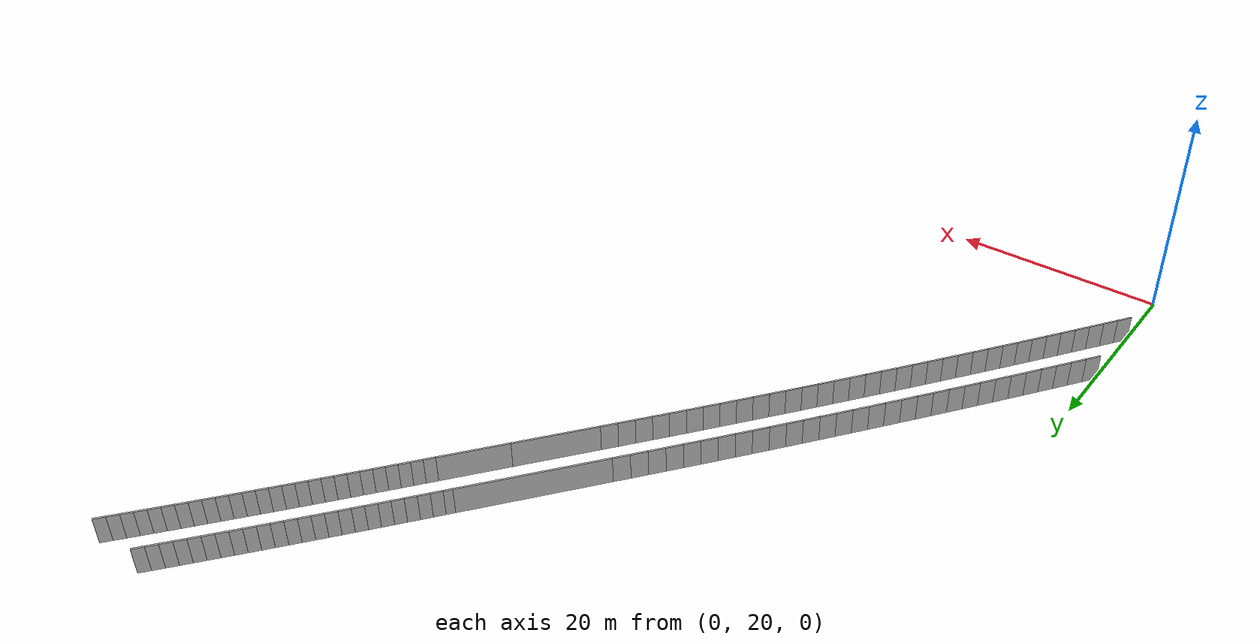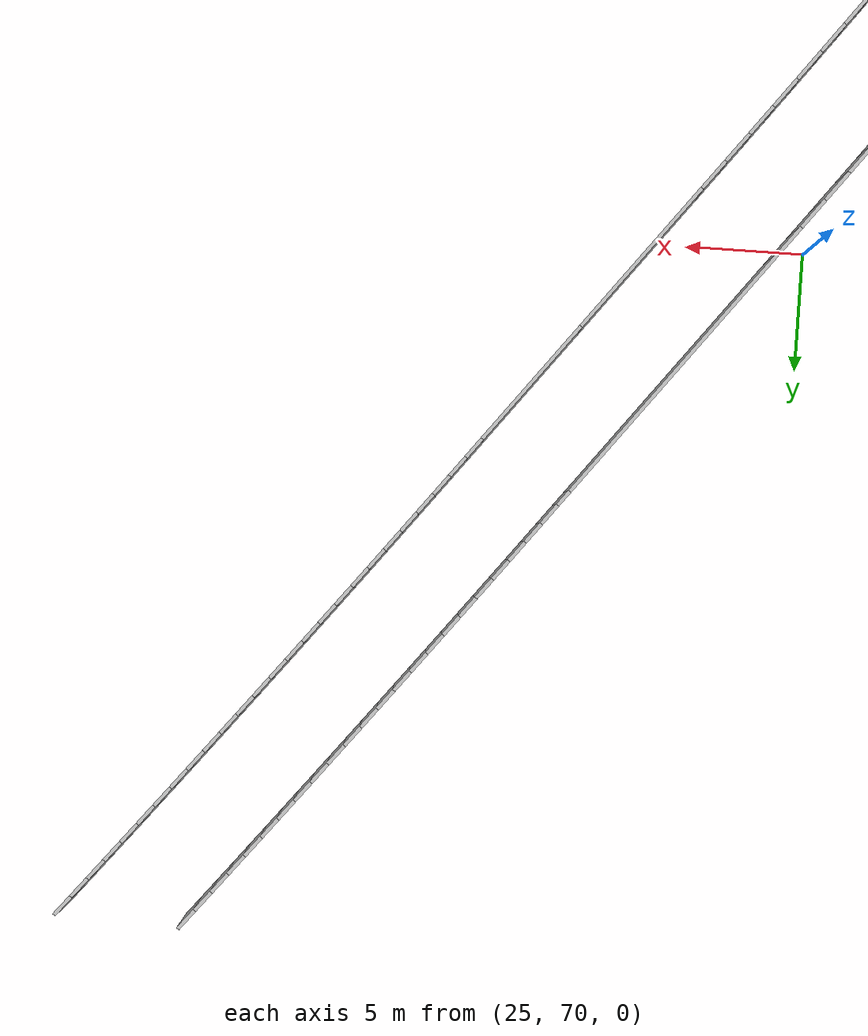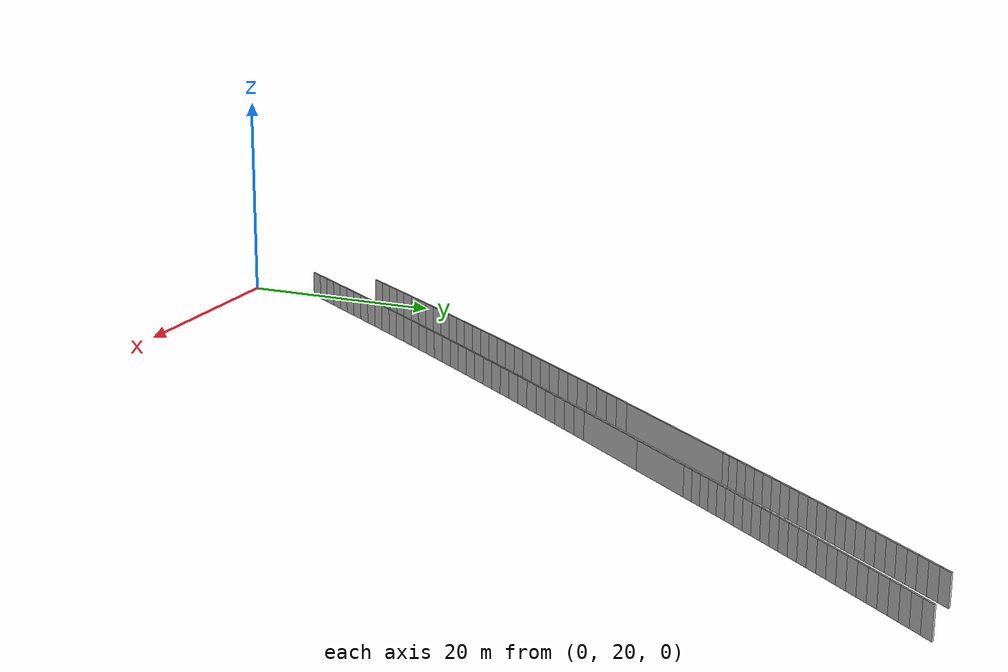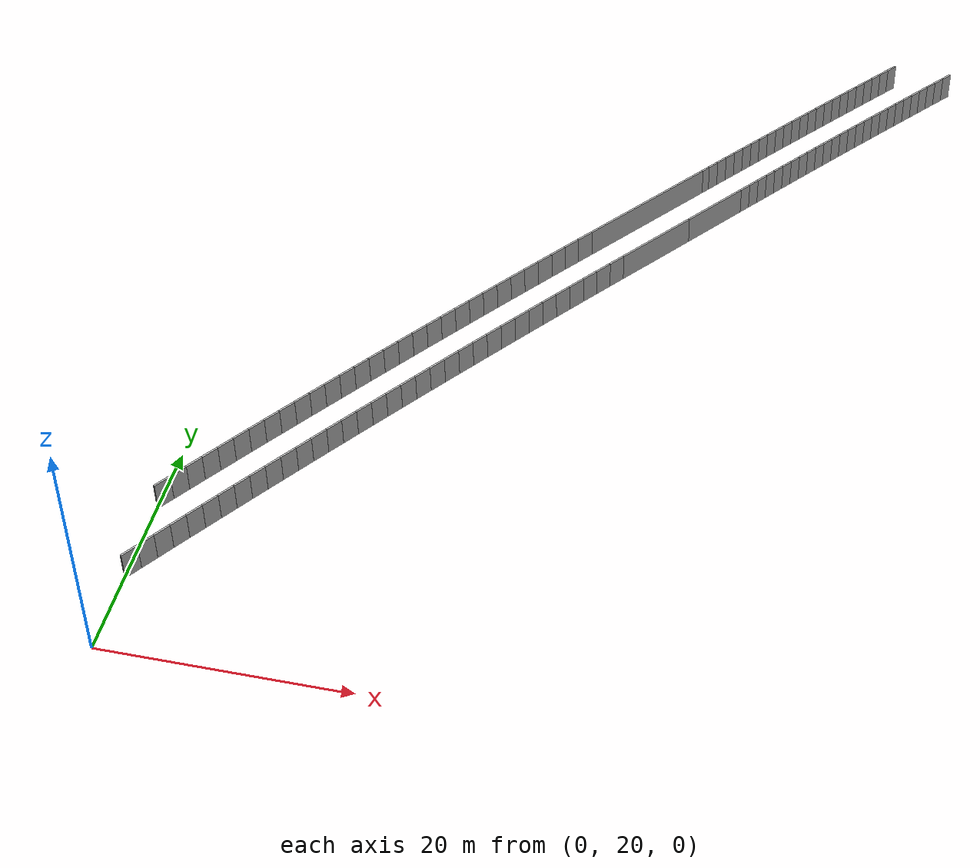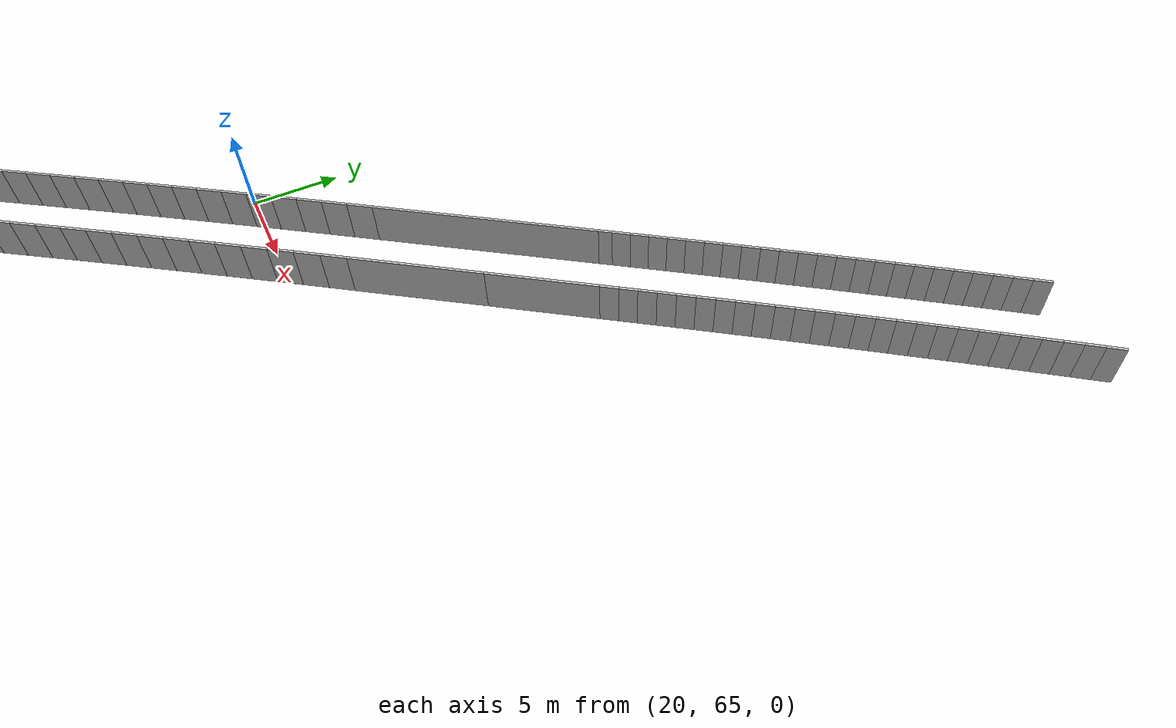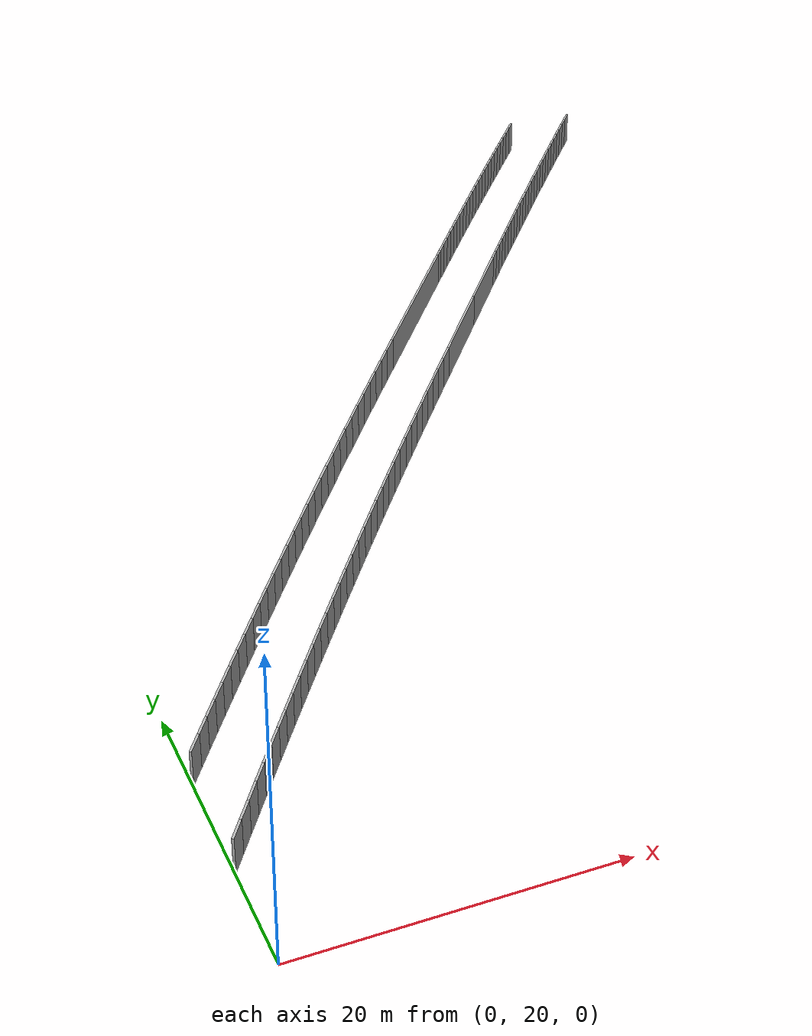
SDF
<?xml version="1.0" ?>
<sdf version="1.6">
  <model name="sps_0318">
    <pose frame="">0 0 0 0 -0 0</pose>
    <static>1</static>
    <self_collide>0</self_collide>
    <allow_auto_disable>0</allow_auto_disable>
    <link name="Wall298">
      <kinematic>0</kinematic>
      <gravity>1</gravity>
      <self_collide>0</self_collide>
      <collision name="collision">
        <geometry>
          <box>
            <size>7.56129 0.15 2.5</size>
          </box>
        </geometry>
        <pose frame="">0 0 0 0 -0 0</pose>
      </collision>
      <visual name="visual">
        <geometry>
          <box>
            <size>7.56129 0.15 2.5</size>
          </box>
        </geometry>
        <pose frame="">0 0 0 0 -0 0</pose>
        <cast_shadows>1</cast_shadows>
        <transparency>0.0</transparency>
      </visual>
      <pose frame="">32.1695 71.0881 1.25 0 -0 0.916836</pose>
    </link>
    <link name="Wall299">
      <kinematic>0</kinematic>
      <gravity>1</gravity>
      <self_collide>0</self_collide>
      <collision name="collision">
        <geometry>
          <box>
            <size>6.16538 0.15 2.5</size>
          </box>
        </geometry>
        <pose frame="">0 0 0 0 -0 0</pose>
      </collision>
      <visual name="visual">
        <geometry>
          <box>
            <size>6.16538 0.15 2.5</size>
          </box>
        </geometry>
        <pose frame="">0 0 0 0 -0 0</pose>
        <cast_shadows>1</cast_shadows>
        <transparency>0.0</transparency>
      </visual>
      <pose frame="">36.3447 76.5354 1.25 0 -0 0.916836</pose>
    </link>
    <link name="Wall442">
      <kinematic>0</kinematic>
      <gravity>1</gravity>
      <self_collide>0</self_collide>
      <collision name="collision">
        <geometry>
          <box>
            <size>0.759106 0.15 2.5</size>
          </box>
        </geometry>
        <pose frame="">0 0 0 0 -0 0</pose>
      </collision>
      <visual name="visual">
        <geometry>
          <box>
            <size>0.759106 0.15 2.5</size>
          </box>
        </geometry>
        <pose frame="">0 0 0 0 -0 0</pose>
        <cast_shadows>1</cast_shadows>
        <transparency>0.0</transparency>
      </visual>
      <pose frame="">34.7003 81.1949 1.25 0 0 -2.22476</pose>
    </link>
    <link name="Wall443">
      <kinematic>0</kinematic>
      <gravity>1</gravity>
      <self_collide>0</self_collide>
      <collision name="collision">
        <geometry>
          <box>
            <size>12.9573 0.15 2.5</size>
          </box>
        </geometry>
        <pose frame="">0 0 0 0 -0 0</pose>
      </collision>
      <visual name="visual">
        <geometry>
          <box>
            <size>12.9573 0.15 2.5</size>
          </box>
        </geometry>
        <pose frame="">0 0 0 0 -0 0</pose>
        <cast_shadows>1</cast_shadows>
        <transparency>0.0</transparency>
      </visual>
      <pose frame="">30.5283 75.7517 1.25 0 0 -2.22476</pose>
    </link>
    <link name="Wall4835">
      <kinematic>0</kinematic>
      <gravity>1</gravity>
      <self_collide>0</self_collide>
      <collision name="collision">
        <geometry>
          <box>
            <size>1.4966 0.15 2.5</size>
          </box>
        </geometry>
        <pose frame="">0 0 0 0 -0 0</pose>
      </collision>
      <visual name="visual">
        <geometry>
          <box>
            <size>1.4966 0.15 2.5</size>
          </box>
        </geometry>
        <pose frame="">0 0 0 0 -0 0</pose>
        <cast_shadows>1</cast_shadows>
        <transparency>0.0</transparency>
      </visual>
      <pose frame="">29.4143 67.4937 1.25 0 0 -2.22504</pose>
    </link>
    <link name="Wall4836">
      <kinematic>0</kinematic>
      <gravity>1</gravity>
      <self_collide>0</self_collide>
      <collision name="collision">
        <geometry>
          <box>
            <size>1.49643 0.15 2.5</size>
          </box>
        </geometry>
        <pose frame="">0 0 0 0 -0 0</pose>
      </collision>
      <visual name="visual">
        <geometry>
          <box>
            <size>1.49643 0.15 2.5</size>
          </box>
        </geometry>
        <pose frame="">0 0 0 0 -0 0</pose>
        <cast_shadows>1</cast_shadows>
        <transparency>0.0</transparency>
      </visual>
      <pose frame="">28.5045 66.3055 1.25 0 0 -2.22348</pose>
    </link>
    <link name="Wall4837">
      <kinematic>0</kinematic>
      <gravity>1</gravity>
      <self_collide>0</self_collide>
      <collision name="collision">
        <geometry>
          <box>
            <size>1.49642 0.15 2.5</size>
          </box>
        </geometry>
        <pose frame="">0 0 0 0 -0 0</pose>
      </collision>
      <visual name="visual">
        <geometry>
          <box>
            <size>1.49642 0.15 2.5</size>
          </box>
        </geometry>
        <pose frame="">0 0 0 0 -0 0</pose>
        <cast_shadows>1</cast_shadows>
        <transparency>0.0</transparency>
      </visual>
      <pose frame="">27.5967 65.1159 1.25 0 0 -2.22179</pose>
    </link>
    <link name="Wall4838">
      <kinematic>0</kinematic>
      <gravity>1</gravity>
      <self_collide>0</self_collide>
      <collision name="collision">
        <geometry>
          <box>
            <size>1.49666 0.15 2.5</size>
          </box>
        </geometry>
        <pose frame="">0 0 0 0 -0 0</pose>
      </collision>
      <visual name="visual">
        <geometry>
          <box>
            <size>1.49666 0.15 2.5</size>
          </box>
        </geometry>
        <pose frame="">0 0 0 0 -0 0</pose>
        <cast_shadows>1</cast_shadows>
        <transparency>0.0</transparency>
      </visual>
      <pose frame="">26.6908 63.9247 1.25 0 0 -2.22019</pose>
    </link>
    <link name="Wall4839">
      <kinematic>0</kinematic>
      <gravity>1</gravity>
      <self_collide>0</self_collide>
      <collision name="collision">
        <geometry>
          <box>
            <size>1.49647 0.15 2.5</size>
          </box>
        </geometry>
        <pose frame="">0 0 0 0 -0 0</pose>
      </collision>
      <visual name="visual">
        <geometry>
          <box>
            <size>1.49647 0.15 2.5</size>
          </box>
        </geometry>
        <pose frame="">0 0 0 0 -0 0</pose>
        <cast_shadows>1</cast_shadows>
        <transparency>0.0</transparency>
      </visual>
      <pose frame="">25.7866 62.7321 1.25 0 0 -2.21874</pose>
    </link>
    <link name="Wall4840">
      <kinematic>0</kinematic>
      <gravity>1</gravity>
      <self_collide>0</self_collide>
      <collision name="collision">
        <geometry>
          <box>
            <size>1.49647 0.15 2.5</size>
          </box>
        </geometry>
        <pose frame="">0 0 0 0 -0 0</pose>
      </collision>
      <visual name="visual">
        <geometry>
          <box>
            <size>1.49647 0.15 2.5</size>
          </box>
        </geometry>
        <pose frame="">0 0 0 0 -0 0</pose>
        <cast_shadows>1</cast_shadows>
        <transparency>0.0</transparency>
      </visual>
      <pose frame="">24.8845 61.5381 1.25 0 0 -2.21691</pose>
    </link>
    <link name="Wall4841">
      <kinematic>0</kinematic>
      <gravity>1</gravity>
      <self_collide>0</self_collide>
      <collision name="collision">
        <geometry>
          <box>
            <size>1.49658 0.15 2.5</size>
          </box>
        </geometry>
        <pose frame="">0 0 0 0 -0 0</pose>
      </collision>
      <visual name="visual">
        <geometry>
          <box>
            <size>1.49658 0.15 2.5</size>
          </box>
        </geometry>
        <pose frame="">0 0 0 0 -0 0</pose>
        <cast_shadows>1</cast_shadows>
        <transparency>0.0</transparency>
      </visual>
      <pose frame="">23.9843 60.3426 1.25 0 0 -2.21552</pose>
    </link>
    <link name="Wall4842">
      <kinematic>0</kinematic>
      <gravity>1</gravity>
      <self_collide>0</self_collide>
      <collision name="collision">
        <geometry>
          <box>
            <size>1.49655 0.15 2.5</size>
          </box>
        </geometry>
        <pose frame="">0 0 0 0 -0 0</pose>
      </collision>
      <visual name="visual">
        <geometry>
          <box>
            <size>1.49655 0.15 2.5</size>
          </box>
        </geometry>
        <pose frame="">0 0 0 0 -0 0</pose>
        <cast_shadows>1</cast_shadows>
        <transparency>0.0</transparency>
      </visual>
      <pose frame="">23.0859 59.1457 1.25 0 0 -2.21386</pose>
    </link>
    <link name="Wall4843">
      <kinematic>0</kinematic>
      <gravity>1</gravity>
      <self_collide>0</self_collide>
      <collision name="collision">
        <geometry>
          <box>
            <size>1.49687 0.15 2.5</size>
          </box>
        </geometry>
        <pose frame="">0 0 0 0 -0 0</pose>
      </collision>
      <visual name="visual">
        <geometry>
          <box>
            <size>1.49687 0.15 2.5</size>
          </box>
        </geometry>
        <pose frame="">0 0 0 0 -0 0</pose>
        <cast_shadows>1</cast_shadows>
        <transparency>0.0</transparency>
      </visual>
      <pose frame="">22.1894 57.9472 1.25 0 0 -2.21217</pose>
    </link>
    <link name="Wall4844">
      <kinematic>0</kinematic>
      <gravity>1</gravity>
      <self_collide>0</self_collide>
      <collision name="collision">
        <geometry>
          <box>
            <size>1.49648 0.15 2.5</size>
          </box>
        </geometry>
        <pose frame="">0 0 0 0 -0 0</pose>
      </collision>
      <visual name="visual">
        <geometry>
          <box>
            <size>1.49648 0.15 2.5</size>
          </box>
        </geometry>
        <pose frame="">0 0 0 0 -0 0</pose>
        <cast_shadows>1</cast_shadows>
        <transparency>0.0</transparency>
      </visual>
      <pose frame="">21.2949 56.7473 1.25 0 0 -2.21073</pose>
    </link>
    <link name="Wall4845">
      <kinematic>0</kinematic>
      <gravity>1</gravity>
      <self_collide>0</self_collide>
      <collision name="collision">
        <geometry>
          <box>
            <size>1.49646 0.15 2.5</size>
          </box>
        </geometry>
        <pose frame="">0 0 0 0 -0 0</pose>
      </collision>
      <visual name="visual">
        <geometry>
          <box>
            <size>1.49646 0.15 2.5</size>
          </box>
        </geometry>
        <pose frame="">0 0 0 0 -0 0</pose>
        <cast_shadows>1</cast_shadows>
        <transparency>0.0</transparency>
      </visual>
      <pose frame="">20.4022 55.5462 1.25 0 0 -2.20907</pose>
    </link>
    <link name="Wall4846">
      <kinematic>0</kinematic>
      <gravity>1</gravity>
      <self_collide>0</self_collide>
      <collision name="collision">
        <geometry>
          <box>
            <size>1.49659 0.15 2.5</size>
          </box>
        </geometry>
        <pose frame="">0 0 0 0 -0 0</pose>
      </collision>
      <visual name="visual">
        <geometry>
          <box>
            <size>1.49659 0.15 2.5</size>
          </box>
        </geometry>
        <pose frame="">0 0 0 0 -0 0</pose>
        <cast_shadows>1</cast_shadows>
        <transparency>0.0</transparency>
      </visual>
      <pose frame="">19.5114 54.3437 1.25 0 0 -2.20768</pose>
    </link>
    <link name="Wall4847">
      <kinematic>0</kinematic>
      <gravity>1</gravity>
      <self_collide>0</self_collide>
      <collision name="collision">
        <geometry>
          <box>
            <size>1.49653 0.15 2.5</size>
          </box>
        </geometry>
        <pose frame="">0 0 0 0 -0 0</pose>
      </collision>
      <visual name="visual">
        <geometry>
          <box>
            <size>1.49653 0.15 2.5</size>
          </box>
        </geometry>
        <pose frame="">0 0 0 0 -0 0</pose>
        <cast_shadows>1</cast_shadows>
        <transparency>0.0</transparency>
      </visual>
      <pose frame="">18.6226 53.1397 1.25 0 0 -2.20584</pose>
    </link>
    <link name="Wall4848">
      <kinematic>0</kinematic>
      <gravity>1</gravity>
      <self_collide>0</self_collide>
      <collision name="collision">
        <geometry>
          <box>
            <size>1.49646 0.15 2.5</size>
          </box>
        </geometry>
        <pose frame="">0 0 0 0 -0 0</pose>
      </collision>
      <visual name="visual">
        <geometry>
          <box>
            <size>1.49646 0.15 2.5</size>
          </box>
        </geometry>
        <pose frame="">0 0 0 0 -0 0</pose>
        <cast_shadows>1</cast_shadows>
        <transparency>0.0</transparency>
      </visual>
      <pose frame="">17.7357 51.9343 1.25 0 0 -2.2044</pose>
    </link>
    <link name="Wall4849">
      <kinematic>0</kinematic>
      <gravity>1</gravity>
      <self_collide>0</self_collide>
      <collision name="collision">
        <geometry>
          <box>
            <size>1.49663 0.15 2.5</size>
          </box>
        </geometry>
        <pose frame="">0 0 0 0 -0 0</pose>
      </collision>
      <visual name="visual">
        <geometry>
          <box>
            <size>1.49663 0.15 2.5</size>
          </box>
        </geometry>
        <pose frame="">0 0 0 0 -0 0</pose>
        <cast_shadows>1</cast_shadows>
        <transparency>0.0</transparency>
      </visual>
      <pose frame="">16.8507 50.7275 1.25 0 0 -2.2027</pose>
    </link>
    <link name="Wall4850">
      <kinematic>0</kinematic>
      <gravity>1</gravity>
      <self_collide>0</self_collide>
      <collision name="collision">
        <geometry>
          <box>
            <size>1.49638 0.15 2.5</size>
          </box>
        </geometry>
        <pose frame="">0 0 0 0 -0 0</pose>
      </collision>
      <visual name="visual">
        <geometry>
          <box>
            <size>1.49638 0.15 2.5</size>
          </box>
        </geometry>
        <pose frame="">0 0 0 0 -0 0</pose>
        <cast_shadows>1</cast_shadows>
        <transparency>0.0</transparency>
      </visual>
      <pose frame="">15.9676 49.5193 1.25 0 0 -2.20116</pose>
    </link>
    <link name="Wall4851">
      <kinematic>0</kinematic>
      <gravity>1</gravity>
      <self_collide>0</self_collide>
      <collision name="collision">
        <geometry>
          <box>
            <size>1.49655 0.15 2.5</size>
          </box>
        </geometry>
        <pose frame="">0 0 0 0 -0 0</pose>
      </collision>
      <visual name="visual">
        <geometry>
          <box>
            <size>1.49655 0.15 2.5</size>
          </box>
        </geometry>
        <pose frame="">0 0 0 0 -0 0</pose>
        <cast_shadows>1</cast_shadows>
        <transparency>0.0</transparency>
      </visual>
      <pose frame="">15.0864 48.3098 1.25 0 0 -2.19971</pose>
    </link>
    <link name="Wall4852">
      <kinematic>0</kinematic>
      <gravity>1</gravity>
      <self_collide>0</self_collide>
      <collision name="collision">
        <geometry>
          <box>
            <size>1.49657 0.15 2.5</size>
          </box>
        </geometry>
        <pose frame="">0 0 0 0 -0 0</pose>
      </collision>
      <visual name="visual">
        <geometry>
          <box>
            <size>1.49657 0.15 2.5</size>
          </box>
        </geometry>
        <pose frame="">0 0 0 0 -0 0</pose>
        <cast_shadows>1</cast_shadows>
        <transparency>0.0</transparency>
      </visual>
      <pose frame="">14.2071 47.0988 1.25 0 0 -2.19793</pose>
    </link>
    <link name="Wall4853">
      <kinematic>0</kinematic>
      <gravity>1</gravity>
      <self_collide>0</self_collide>
      <collision name="collision">
        <geometry>
          <box>
            <size>1.49641 0.15 2.5</size>
          </box>
        </geometry>
        <pose frame="">0 0 0 0 -0 0</pose>
      </collision>
      <visual name="visual">
        <geometry>
          <box>
            <size>1.49641 0.15 2.5</size>
          </box>
        </geometry>
        <pose frame="">0 0 0 0 -0 0</pose>
        <cast_shadows>1</cast_shadows>
        <transparency>0.0</transparency>
      </visual>
      <pose frame="">13.3299 45.8864 1.25 0 0 -2.19646</pose>
    </link>
    <link name="Wall4854">
      <kinematic>0</kinematic>
      <gravity>1</gravity>
      <self_collide>0</self_collide>
      <collision name="collision">
        <geometry>
          <box>
            <size>1.49663 0.15 2.5</size>
          </box>
        </geometry>
        <pose frame="">0 0 0 0 -0 0</pose>
      </collision>
      <visual name="visual">
        <geometry>
          <box>
            <size>1.49663 0.15 2.5</size>
          </box>
        </geometry>
        <pose frame="">0 0 0 0 -0 0</pose>
        <cast_shadows>1</cast_shadows>
        <transparency>0.0</transparency>
      </visual>
      <pose frame="">12.4545 44.6726 1.25 0 0 -2.19479</pose>
    </link>
    <link name="Wall4855">
      <kinematic>0</kinematic>
      <gravity>1</gravity>
      <self_collide>0</self_collide>
      <collision name="collision">
        <geometry>
          <box>
            <size>1.49652 0.15 2.5</size>
          </box>
        </geometry>
        <pose frame="">0 0 0 0 -0 0</pose>
      </collision>
      <visual name="visual">
        <geometry>
          <box>
            <size>1.49652 0.15 2.5</size>
          </box>
        </geometry>
        <pose frame="">0 0 0 0 -0 0</pose>
        <cast_shadows>1</cast_shadows>
        <transparency>0.0</transparency>
      </visual>
      <pose frame="">11.581 43.4574 1.25 0 0 -2.19328</pose>
    </link>
    <link name="Wall4856">
      <kinematic>0</kinematic>
      <gravity>1</gravity>
      <self_collide>0</self_collide>
      <collision name="collision">
        <geometry>
          <box>
            <size>1.49667 0.15 2.5</size>
          </box>
        </geometry>
        <pose frame="">0 0 0 0 -0 0</pose>
      </collision>
      <visual name="visual">
        <geometry>
          <box>
            <size>1.49667 0.15 2.5</size>
          </box>
        </geometry>
        <pose frame="">0 0 0 0 -0 0</pose>
        <cast_shadows>1</cast_shadows>
        <transparency>0.0</transparency>
      </visual>
      <pose frame="">10.7093 42.2409 1.25 0 0 -2.19181</pose>
    </link>
    <link name="Wall4857">
      <kinematic>0</kinematic>
      <gravity>1</gravity>
      <self_collide>0</self_collide>
      <collision name="collision">
        <geometry>
          <box>
            <size>1.4963 0.15 2.5</size>
          </box>
        </geometry>
        <pose frame="">0 0 0 0 -0 0</pose>
      </collision>
      <visual name="visual">
        <geometry>
          <box>
            <size>1.4963 0.15 2.5</size>
          </box>
        </geometry>
        <pose frame="">0 0 0 0 -0 0</pose>
        <cast_shadows>1</cast_shadows>
        <transparency>0.0</transparency>
      </visual>
      <pose frame="">9.83953 41.0231 1.25 0 0 -2.19013</pose>
    </link>
    <link name="Wall4858">
      <kinematic>0</kinematic>
      <gravity>1</gravity>
      <self_collide>0</self_collide>
      <collision name="collision">
        <geometry>
          <box>
            <size>1.49653 0.15 2.5</size>
          </box>
        </geometry>
        <pose frame="">0 0 0 0 -0 0</pose>
      </collision>
      <visual name="visual">
        <geometry>
          <box>
            <size>1.49653 0.15 2.5</size>
          </box>
        </geometry>
        <pose frame="">0 0 0 0 -0 0</pose>
        <cast_shadows>1</cast_shadows>
        <transparency>0.0</transparency>
      </visual>
      <pose frame="">8.97185 39.8039 1.25 0 0 -2.18852</pose>
    </link>
    <link name="Wall4859">
      <kinematic>0</kinematic>
      <gravity>1</gravity>
      <self_collide>0</self_collide>
      <collision name="collision">
        <geometry>
          <box>
            <size>1.4967 0.15 2.5</size>
          </box>
        </geometry>
        <pose frame="">0 0 0 0 -0 0</pose>
      </collision>
      <visual name="visual">
        <geometry>
          <box>
            <size>1.4967 0.15 2.5</size>
          </box>
        </geometry>
        <pose frame="">0 0 0 0 -0 0</pose>
        <cast_shadows>1</cast_shadows>
        <transparency>0.0</transparency>
      </visual>
      <pose frame="">8.10598 38.5832 1.25 0 0 -2.18699</pose>
    </link>
    <link name="Wall4860">
      <kinematic>0</kinematic>
      <gravity>1</gravity>
      <self_collide>0</self_collide>
      <collision name="collision">
        <geometry>
          <box>
            <size>1.49641 0.15 2.5</size>
          </box>
        </geometry>
        <pose frame="">0 0 0 0 -0 0</pose>
      </collision>
      <visual name="visual">
        <geometry>
          <box>
            <size>1.49641 0.15 2.5</size>
          </box>
        </geometry>
        <pose frame="">0 0 0 0 -0 0</pose>
        <cast_shadows>1</cast_shadows>
        <transparency>0.0</transparency>
      </visual>
      <pose frame="">7.24206 37.3612 1.25 0 0 -2.18537</pose>
    </link>
    <link name="Wall4861">
      <kinematic>0</kinematic>
      <gravity>1</gravity>
      <self_collide>0</self_collide>
      <collision name="collision">
        <geometry>
          <box>
            <size>1.49662 0.15 2.5</size>
          </box>
        </geometry>
        <pose frame="">0 0 0 0 -0 0</pose>
      </collision>
      <visual name="visual">
        <geometry>
          <box>
            <size>1.49662 0.15 2.5</size>
          </box>
        </geometry>
        <pose frame="">0 0 0 0 -0 0</pose>
        <cast_shadows>1</cast_shadows>
        <transparency>0.0</transparency>
      </visual>
      <pose frame="">6.38015 36.1378 1.25 0 0 -2.18373</pose>
    </link>
    <link name="Wall4862">
      <kinematic>0</kinematic>
      <gravity>1</gravity>
      <self_collide>0</self_collide>
      <collision name="collision">
        <geometry>
          <box>
            <size>1.4965 0.15 2.5</size>
          </box>
        </geometry>
        <pose frame="">0 0 0 0 -0 0</pose>
      </collision>
      <visual name="visual">
        <geometry>
          <box>
            <size>1.4965 0.15 2.5</size>
          </box>
        </geometry>
        <pose frame="">0 0 0 0 -0 0</pose>
        <cast_shadows>1</cast_shadows>
        <transparency>0.0</transparency>
      </visual>
      <pose frame="">5.52016 34.913 1.25 0 0 -2.18219</pose>
    </link>
    <link name="Wall4863">
      <kinematic>0</kinematic>
      <gravity>1</gravity>
      <self_collide>0</self_collide>
      <collision name="collision">
        <geometry>
          <box>
            <size>1.49634 0.15 2.5</size>
          </box>
        </geometry>
        <pose frame="">0 0 0 0 -0 0</pose>
      </collision>
      <visual name="visual">
        <geometry>
          <box>
            <size>1.49634 0.15 2.5</size>
          </box>
        </geometry>
        <pose frame="">0 0 0 0 -0 0</pose>
        <cast_shadows>1</cast_shadows>
        <transparency>0.0</transparency>
      </visual>
      <pose frame="">4.66216 33.687 1.25 0 0 -2.18062</pose>
    </link>
    <link name="Wall4864">
      <kinematic>0</kinematic>
      <gravity>1</gravity>
      <self_collide>0</self_collide>
      <collision name="collision">
        <geometry>
          <box>
            <size>1.49663 0.15 2.5</size>
          </box>
        </geometry>
        <pose frame="">0 0 0 0 -0 0</pose>
      </collision>
      <visual name="visual">
        <geometry>
          <box>
            <size>1.49663 0.15 2.5</size>
          </box>
        </geometry>
        <pose frame="">0 0 0 0 -0 0</pose>
        <cast_shadows>1</cast_shadows>
        <transparency>0.0</transparency>
      </visual>
      <pose frame="">3.80605 32.4596 1.25 0 0 -2.17905</pose>
    </link>
    <link name="Wall4865">
      <kinematic>0</kinematic>
      <gravity>1</gravity>
      <self_collide>0</self_collide>
      <collision name="collision">
        <geometry>
          <box>
            <size>1.49659 0.15 2.5</size>
          </box>
        </geometry>
        <pose frame="">0 0 0 0 -0 0</pose>
      </collision>
      <visual name="visual">
        <geometry>
          <box>
            <size>1.49659 0.15 2.5</size>
          </box>
        </geometry>
        <pose frame="">0 0 0 0 -0 0</pose>
        <cast_shadows>1</cast_shadows>
        <transparency>0.0</transparency>
      </visual>
      <pose frame="">2.95183 31.2307 1.25 0 0 -2.17743</pose>
    </link>
    <link name="Wall4866">
      <kinematic>0</kinematic>
      <gravity>1</gravity>
      <self_collide>0</self_collide>
      <collision name="collision">
        <geometry>
          <box>
            <size>1.49649 0.15 2.5</size>
          </box>
        </geometry>
        <pose frame="">0 0 0 0 -0 0</pose>
      </collision>
      <visual name="visual">
        <geometry>
          <box>
            <size>1.49649 0.15 2.5</size>
          </box>
        </geometry>
        <pose frame="">0 0 0 0 -0 0</pose>
        <cast_shadows>1</cast_shadows>
        <transparency>0.0</transparency>
      </visual>
      <pose frame="">2.09963 30.0005 1.25 0 0 -2.17584</pose>
    </link>
    <link name="Wall4867">
      <kinematic>0</kinematic>
      <gravity>1</gravity>
      <self_collide>0</self_collide>
      <collision name="collision">
        <geometry>
          <box>
            <size>1.49645 0.15 2.5</size>
          </box>
        </geometry>
        <pose frame="">0 0 0 0 -0 0</pose>
      </collision>
      <visual name="visual">
        <geometry>
          <box>
            <size>1.49645 0.15 2.5</size>
          </box>
        </geometry>
        <pose frame="">0 0 0 0 -0 0</pose>
        <cast_shadows>1</cast_shadows>
        <transparency>0.0</transparency>
      </visual>
      <pose frame="">1.24944 28.769 1.25 0 0 -2.17422</pose>
    </link>
    <link name="Wall4868">
      <kinematic>0</kinematic>
      <gravity>1</gravity>
      <self_collide>0</self_collide>
      <collision name="collision">
        <geometry>
          <box>
            <size>1.49666 0.15 2.5</size>
          </box>
        </geometry>
        <pose frame="">0 0 0 0 -0 0</pose>
      </collision>
      <visual name="visual">
        <geometry>
          <box>
            <size>1.49666 0.15 2.5</size>
          </box>
        </geometry>
        <pose frame="">0 0 0 0 -0 0</pose>
        <cast_shadows>1</cast_shadows>
        <transparency>0.0</transparency>
      </visual>
      <pose frame="">0.401145 27.5361 1.25 0 0 -2.17269</pose>
    </link>
    <link name="Wall6631">
      <kinematic>0</kinematic>
      <gravity>1</gravity>
      <self_collide>0</self_collide>
      <collision name="collision">
        <geometry>
          <box>
            <size>1.5031 0.15 2.5</size>
          </box>
        </geometry>
        <pose frame="">0 0 0 0 -0 0</pose>
      </collision>
      <visual name="visual">
        <geometry>
          <box>
            <size>1.5031 0.15 2.5</size>
          </box>
        </geometry>
        <pose frame="">0 0 0 0 -0 0</pose>
        <cast_shadows>1</cast_shadows>
        <transparency>0.0</transparency>
      </visual>
      <pose frame="">26.1298 70.0133 1.25 0 0 -2.22494</pose>
    </link>
    <link name="Wall6632">
      <kinematic>0</kinematic>
      <gravity>1</gravity>
      <self_collide>0</self_collide>
      <collision name="collision">
        <geometry>
          <box>
            <size>1.50314 0.15 2.5</size>
          </box>
        </geometry>
        <pose frame="">0 0 0 0 -0 0</pose>
      </collision>
      <visual name="visual">
        <geometry>
          <box>
            <size>1.50314 0.15 2.5</size>
          </box>
        </geometry>
        <pose frame="">0 0 0 0 -0 0</pose>
        <cast_shadows>1</cast_shadows>
        <transparency>0.0</transparency>
      </visual>
      <pose frame="">25.2161 68.8197 1.25 0 0 -2.22324</pose>
    </link>
    <link name="Wall6633">
      <kinematic>0</kinematic>
      <gravity>1</gravity>
      <self_collide>0</self_collide>
      <collision name="collision">
        <geometry>
          <box>
            <size>1.503 0.15 2.5</size>
          </box>
        </geometry>
        <pose frame="">0 0 0 0 -0 0</pose>
      </collision>
      <visual name="visual">
        <geometry>
          <box>
            <size>1.503 0.15 2.5</size>
          </box>
        </geometry>
        <pose frame="">0 0 0 0 -0 0</pose>
        <cast_shadows>1</cast_shadows>
        <transparency>0.0</transparency>
      </visual>
      <pose frame="">24.3045 67.6247 1.25 0 0 -2.22178</pose>
    </link>
    <link name="Wall6634">
      <kinematic>0</kinematic>
      <gravity>1</gravity>
      <self_collide>0</self_collide>
      <collision name="collision">
        <geometry>
          <box>
            <size>1.50319 0.15 2.5</size>
          </box>
        </geometry>
        <pose frame="">0 0 0 0 -0 0</pose>
      </collision>
      <visual name="visual">
        <geometry>
          <box>
            <size>1.50319 0.15 2.5</size>
          </box>
        </geometry>
        <pose frame="">0 0 0 0 -0 0</pose>
        <cast_shadows>1</cast_shadows>
        <transparency>0.0</transparency>
      </visual>
      <pose frame="">23.3946 66.4283 1.25 0 0 -2.2202</pose>
    </link>
    <link name="Wall6635">
      <kinematic>0</kinematic>
      <gravity>1</gravity>
      <self_collide>0</self_collide>
      <collision name="collision">
        <geometry>
          <box>
            <size>1.50327 0.15 2.5</size>
          </box>
        </geometry>
        <pose frame="">0 0 0 0 -0 0</pose>
      </collision>
      <visual name="visual">
        <geometry>
          <box>
            <size>1.50327 0.15 2.5</size>
          </box>
        </geometry>
        <pose frame="">0 0 0 0 -0 0</pose>
        <cast_shadows>1</cast_shadows>
        <transparency>0.0</transparency>
      </visual>
      <pose frame="">22.4866 65.2303 1.25 0 0 -2.21853</pose>
    </link>
    <link name="Wall6636">
      <kinematic>0</kinematic>
      <gravity>1</gravity>
      <self_collide>0</self_collide>
      <collision name="collision">
        <geometry>
          <box>
            <size>1.50309 0.15 2.5</size>
          </box>
        </geometry>
        <pose frame="">0 0 0 0 -0 0</pose>
      </collision>
      <visual name="visual">
        <geometry>
          <box>
            <size>1.50309 0.15 2.5</size>
          </box>
        </geometry>
        <pose frame="">0 0 0 0 -0 0</pose>
        <cast_shadows>1</cast_shadows>
        <transparency>0.0</transparency>
      </visual>
      <pose frame="">21.5804 64.0309 1.25 0 0 -2.21709</pose>
    </link>
    <link name="Wall6637">
      <kinematic>0</kinematic>
      <gravity>1</gravity>
      <self_collide>0</self_collide>
      <collision name="collision">
        <geometry>
          <box>
            <size>1.50305 0.15 2.5</size>
          </box>
        </geometry>
        <pose frame="">0 0 0 0 -0 0</pose>
      </collision>
      <visual name="visual">
        <geometry>
          <box>
            <size>1.50305 0.15 2.5</size>
          </box>
        </geometry>
        <pose frame="">0 0 0 0 -0 0</pose>
        <cast_shadows>1</cast_shadows>
        <transparency>0.0</transparency>
      </visual>
      <pose frame="">20.6762 62.8302 1.25 0 0 -2.21543</pose>
    </link>
    <link name="Wall6638">
      <kinematic>0</kinematic>
      <gravity>1</gravity>
      <self_collide>0</self_collide>
      <collision name="collision">
        <geometry>
          <box>
            <size>1.50322 0.15 2.5</size>
          </box>
        </geometry>
        <pose frame="">0 0 0 0 -0 0</pose>
      </collision>
      <visual name="visual">
        <geometry>
          <box>
            <size>1.50322 0.15 2.5</size>
          </box>
        </geometry>
        <pose frame="">0 0 0 0 -0 0</pose>
        <cast_shadows>1</cast_shadows>
        <transparency>0.0</transparency>
      </visual>
      <pose frame="">19.7739 61.628 1.25 0 0 -2.21383</pose>
    </link>
    <link name="Wall6639">
      <kinematic>0</kinematic>
      <gravity>1</gravity>
      <self_collide>0</self_collide>
      <collision name="collision">
        <geometry>
          <box>
            <size>1.50314 0.15 2.5</size>
          </box>
        </geometry>
        <pose frame="">0 0 0 0 -0 0</pose>
      </collision>
      <visual name="visual">
        <geometry>
          <box>
            <size>1.50314 0.15 2.5</size>
          </box>
        </geometry>
        <pose frame="">0 0 0 0 -0 0</pose>
        <cast_shadows>1</cast_shadows>
        <transparency>0.0</transparency>
      </visual>
      <pose frame="">18.8735 60.4244 1.25 0 0 -2.2124</pose>
    </link>
    <link name="Wall6640">
      <kinematic>0</kinematic>
      <gravity>1</gravity>
      <self_collide>0</self_collide>
      <collision name="collision">
        <geometry>
          <box>
            <size>1.5029 0.15 2.5</size>
          </box>
        </geometry>
        <pose frame="">0 0 0 0 -0 0</pose>
      </collision>
      <visual name="visual">
        <geometry>
          <box>
            <size>1.5029 0.15 2.5</size>
          </box>
        </geometry>
        <pose frame="">0 0 0 0 -0 0</pose>
        <cast_shadows>1</cast_shadows>
        <transparency>0.0</transparency>
      </visual>
      <pose frame="">17.975 59.2195 1.25 0 0 -2.21069</pose>
    </link>
    <link name="Wall6641">
      <kinematic>0</kinematic>
      <gravity>1</gravity>
      <self_collide>0</self_collide>
      <collision name="collision">
        <geometry>
          <box>
            <size>1.50302 0.15 2.5</size>
          </box>
        </geometry>
        <pose frame="">0 0 0 0 -0 0</pose>
      </collision>
      <visual name="visual">
        <geometry>
          <box>
            <size>1.50302 0.15 2.5</size>
          </box>
        </geometry>
        <pose frame="">0 0 0 0 -0 0</pose>
        <cast_shadows>1</cast_shadows>
        <transparency>0.0</transparency>
      </visual>
      <pose frame="">17.0785 58.0132 1.25 0 0 -2.20916</pose>
    </link>
    <link name="Wall6642">
      <kinematic>0</kinematic>
      <gravity>1</gravity>
      <self_collide>0</self_collide>
      <collision name="collision">
        <geometry>
          <box>
            <size>1.50321 0.15 2.5</size>
          </box>
        </geometry>
        <pose frame="">0 0 0 0 -0 0</pose>
      </collision>
      <visual name="visual">
        <geometry>
          <box>
            <size>1.50321 0.15 2.5</size>
          </box>
        </geometry>
        <pose frame="">0 0 0 0 -0 0</pose>
        <cast_shadows>1</cast_shadows>
        <transparency>0.0</transparency>
      </visual>
      <pose frame="">16.1837 56.8054 1.25 0 0 -2.20756</pose>
    </link>
    <link name="Wall6643">
      <kinematic>0</kinematic>
      <gravity>1</gravity>
      <self_collide>0</self_collide>
      <collision name="collision">
        <geometry>
          <box>
            <size>1.50309 0.15 2.5</size>
          </box>
        </geometry>
        <pose frame="">0 0 0 0 -0 0</pose>
      </collision>
      <visual name="visual">
        <geometry>
          <box>
            <size>1.50309 0.15 2.5</size>
          </box>
        </geometry>
        <pose frame="">0 0 0 0 -0 0</pose>
        <cast_shadows>1</cast_shadows>
        <transparency>0.0</transparency>
      </visual>
      <pose frame="">15.2909 55.5961 1.25 0 0 -2.20595</pose>
    </link>
    <link name="Wall6644">
      <kinematic>0</kinematic>
      <gravity>1</gravity>
      <self_collide>0</self_collide>
      <collision name="collision">
        <geometry>
          <box>
            <size>1.50308 0.15 2.5</size>
          </box>
        </geometry>
        <pose frame="">0 0 0 0 -0 0</pose>
      </collision>
      <visual name="visual">
        <geometry>
          <box>
            <size>1.50308 0.15 2.5</size>
          </box>
        </geometry>
        <pose frame="">0 0 0 0 -0 0</pose>
        <cast_shadows>1</cast_shadows>
        <transparency>0.0</transparency>
      </visual>
      <pose frame="">14.4002 54.3854 1.25 0 0 -2.20429</pose>
    </link>
    <link name="Wall6645">
      <kinematic>0</kinematic>
      <gravity>1</gravity>
      <self_collide>0</self_collide>
      <collision name="collision">
        <geometry>
          <box>
            <size>1.50311 0.15 2.5</size>
          </box>
        </geometry>
        <pose frame="">0 0 0 0 -0 0</pose>
      </collision>
      <visual name="visual">
        <geometry>
          <box>
            <size>1.50311 0.15 2.5</size>
          </box>
        </geometry>
        <pose frame="">0 0 0 0 -0 0</pose>
        <cast_shadows>1</cast_shadows>
        <transparency>0.0</transparency>
      </visual>
      <pose frame="">13.5113 53.1733 1.25 0 0 -2.20281</pose>
    </link>
    <link name="Wall6646">
      <kinematic>0</kinematic>
      <gravity>1</gravity>
      <self_collide>0</self_collide>
      <collision name="collision">
        <geometry>
          <box>
            <size>1.50314 0.15 2.5</size>
          </box>
        </geometry>
        <pose frame="">0 0 0 0 -0 0</pose>
      </collision>
      <visual name="visual">
        <geometry>
          <box>
            <size>1.50314 0.15 2.5</size>
          </box>
        </geometry>
        <pose frame="">0 0 0 0 -0 0</pose>
        <cast_shadows>1</cast_shadows>
        <transparency>0.0</transparency>
      </visual>
      <pose frame="">12.6243 51.9598 1.25 0 0 -2.20119</pose>
    </link>
    <link name="Wall6647">
      <kinematic>0</kinematic>
      <gravity>1</gravity>
      <self_collide>0</self_collide>
      <collision name="collision">
        <geometry>
          <box>
            <size>1.50286 0.15 2.5</size>
          </box>
        </geometry>
        <pose frame="">0 0 0 0 -0 0</pose>
      </collision>
      <visual name="visual">
        <geometry>
          <box>
            <size>1.50286 0.15 2.5</size>
          </box>
        </geometry>
        <pose frame="">0 0 0 0 -0 0</pose>
        <cast_shadows>1</cast_shadows>
        <transparency>0.0</transparency>
      </visual>
      <pose frame="">11.7392 50.745 1.25 0 0 -2.19962</pose>
    </link>
    <link name="Wall6648">
      <kinematic>0</kinematic>
      <gravity>1</gravity>
      <self_collide>0</self_collide>
      <collision name="collision">
        <geometry>
          <box>
            <size>1.503 0.15 2.5</size>
          </box>
        </geometry>
        <pose frame="">0 0 0 0 -0 0</pose>
      </collision>
      <visual name="visual">
        <geometry>
          <box>
            <size>1.503 0.15 2.5</size>
          </box>
        </geometry>
        <pose frame="">0 0 0 0 -0 0</pose>
        <cast_shadows>1</cast_shadows>
        <transparency>0.0</transparency>
      </visual>
      <pose frame="">10.8563 49.5288 1.25 0 0 -2.19795</pose>
    </link>
    <link name="Wall6649">
      <kinematic>0</kinematic>
      <gravity>1</gravity>
      <self_collide>0</self_collide>
      <collision name="collision">
        <geometry>
          <box>
            <size>1.50317 0.15 2.5</size>
          </box>
        </geometry>
        <pose frame="">0 0 0 0 -0 0</pose>
      </collision>
      <visual name="visual">
        <geometry>
          <box>
            <size>1.50317 0.15 2.5</size>
          </box>
        </geometry>
        <pose frame="">0 0 0 0 -0 0</pose>
        <cast_shadows>1</cast_shadows>
        <transparency>0.0</transparency>
      </visual>
      <pose frame="">9.97506 48.3111 1.25 0 0 -2.19651</pose>
    </link>
    <link name="Wall6650">
      <kinematic>0</kinematic>
      <gravity>1</gravity>
      <self_collide>0</self_collide>
      <collision name="collision">
        <geometry>
          <box>
            <size>1.50321 0.15 2.5</size>
          </box>
        </geometry>
        <pose frame="">0 0 0 0 -0 0</pose>
      </collision>
      <visual name="visual">
        <geometry>
          <box>
            <size>1.50321 0.15 2.5</size>
          </box>
        </geometry>
        <pose frame="">0 0 0 0 -0 0</pose>
        <cast_shadows>1</cast_shadows>
        <transparency>0.0</transparency>
      </visual>
      <pose frame="">9.09566 47.092 1.25 0 0 -2.19489</pose>
    </link>
    <link name="Wall6651">
      <kinematic>0</kinematic>
      <gravity>1</gravity>
      <self_collide>0</self_collide>
      <collision name="collision">
        <geometry>
          <box>
            <size>1.50313 0.15 2.5</size>
          </box>
        </geometry>
        <pose frame="">0 0 0 0 -0 0</pose>
      </collision>
      <visual name="visual">
        <geometry>
          <box>
            <size>1.50313 0.15 2.5</size>
          </box>
        </geometry>
        <pose frame="">0 0 0 0 -0 0</pose>
        <cast_shadows>1</cast_shadows>
        <transparency>0.0</transparency>
      </visual>
      <pose frame="">8.21825 45.8715 1.25 0 0 -2.19328</pose>
    </link>
    <link name="Wall6652">
      <kinematic>0</kinematic>
      <gravity>1</gravity>
      <self_collide>0</self_collide>
      <collision name="collision">
        <geometry>
          <box>
            <size>1.50295 0.15 2.5</size>
          </box>
        </geometry>
        <pose frame="">0 0 0 0 -0 0</pose>
      </collision>
      <visual name="visual">
        <geometry>
          <box>
            <size>1.50295 0.15 2.5</size>
          </box>
        </geometry>
        <pose frame="">0 0 0 0 -0 0</pose>
        <cast_shadows>1</cast_shadows>
        <transparency>0.0</transparency>
      </visual>
      <pose frame="">7.34286 44.6497 1.25 0 0 -2.19172</pose>
    </link>
    <link name="Wall6653">
      <kinematic>0</kinematic>
      <gravity>1</gravity>
      <self_collide>0</self_collide>
      <collision name="collision">
        <geometry>
          <box>
            <size>1.50321 0.15 2.5</size>
          </box>
        </geometry>
        <pose frame="">0 0 0 0 -0 0</pose>
      </collision>
      <visual name="visual">
        <geometry>
          <box>
            <size>1.50321 0.15 2.5</size>
          </box>
        </geometry>
        <pose frame="">0 0 0 0 -0 0</pose>
        <cast_shadows>1</cast_shadows>
        <transparency>0.0</transparency>
      </visual>
      <pose frame="">6.46935 43.4265 1.25 0 0 -2.19014</pose>
    </link>
    <link name="Wall6654">
      <kinematic>0</kinematic>
      <gravity>1</gravity>
      <self_collide>0</self_collide>
      <collision name="collision">
        <geometry>
          <box>
            <size>1.50299 0.15 2.5</size>
          </box>
        </geometry>
        <pose frame="">0 0 0 0 -0 0</pose>
      </collision>
      <visual name="visual">
        <geometry>
          <box>
            <size>1.50299 0.15 2.5</size>
          </box>
        </geometry>
        <pose frame="">0 0 0 0 -0 0</pose>
        <cast_shadows>1</cast_shadows>
        <transparency>0.0</transparency>
      </visual>
      <pose frame="">5.59774 42.2019 1.25 0 0 -2.18861</pose>
    </link>
    <link name="Wall6655">
      <kinematic>0</kinematic>
      <gravity>1</gravity>
      <self_collide>0</self_collide>
      <collision name="collision">
        <geometry>
          <box>
            <size>1.50317 0.15 2.5</size>
          </box>
        </geometry>
        <pose frame="">0 0 0 0 -0 0</pose>
      </collision>
      <visual name="visual">
        <geometry>
          <box>
            <size>1.50317 0.15 2.5</size>
          </box>
        </geometry>
        <pose frame="">0 0 0 0 -0 0</pose>
        <cast_shadows>1</cast_shadows>
        <transparency>0.0</transparency>
      </visual>
      <pose frame="">4.72814 40.9759 1.25 0 0 -2.18688</pose>
    </link>
    <link name="Wall6656">
      <kinematic>0</kinematic>
      <gravity>1</gravity>
      <self_collide>0</self_collide>
      <collision name="collision">
        <geometry>
          <box>
            <size>1.503 0.15 2.5</size>
          </box>
        </geometry>
        <pose frame="">0 0 0 0 -0 0</pose>
      </collision>
      <visual name="visual">
        <geometry>
          <box>
            <size>1.503 0.15 2.5</size>
          </box>
        </geometry>
        <pose frame="">0 0 0 0 -0 0</pose>
        <cast_shadows>1</cast_shadows>
        <transparency>0.0</transparency>
      </visual>
      <pose frame="">3.86056 39.7485 1.25 0 0 -2.18531</pose>
    </link>
    <link name="Wall6657">
      <kinematic>0</kinematic>
      <gravity>1</gravity>
      <self_collide>0</self_collide>
      <collision name="collision">
        <geometry>
          <box>
            <size>1.50308 0.15 2.5</size>
          </box>
        </geometry>
        <pose frame="">0 0 0 0 -0 0</pose>
      </collision>
      <visual name="visual">
        <geometry>
          <box>
            <size>1.50308 0.15 2.5</size>
          </box>
        </geometry>
        <pose frame="">0 0 0 0 -0 0</pose>
        <cast_shadows>1</cast_shadows>
        <transparency>0.0</transparency>
      </visual>
      <pose frame="">2.99486 38.5198 1.25 0 0 -2.18384</pose>
    </link>
    <link name="Wall6658">
      <kinematic>0</kinematic>
      <gravity>1</gravity>
      <self_collide>0</self_collide>
      <collision name="collision">
        <geometry>
          <box>
            <size>1.50312 0.15 2.5</size>
          </box>
        </geometry>
        <pose frame="">0 0 0 0 -0 0</pose>
      </collision>
      <visual name="visual">
        <geometry>
          <box>
            <size>1.50312 0.15 2.5</size>
          </box>
        </geometry>
        <pose frame="">0 0 0 0 -0 0</pose>
        <cast_shadows>1</cast_shadows>
        <transparency>0.0</transparency>
      </visual>
      <pose frame="">2.13106 37.2897 1.25 0 0 -2.18218</pose>
    </link>
    <link name="Wall6659">
      <kinematic>0</kinematic>
      <gravity>1</gravity>
      <self_collide>0</self_collide>
      <collision name="collision">
        <geometry>
          <box>
            <size>1.5031 0.15 2.5</size>
          </box>
        </geometry>
        <pose frame="">0 0 0 0 -0 0</pose>
      </collision>
      <visual name="visual">
        <geometry>
          <box>
            <size>1.5031 0.15 2.5</size>
          </box>
        </geometry>
        <pose frame="">0 0 0 0 -0 0</pose>
        <cast_shadows>1</cast_shadows>
        <transparency>0.0</transparency>
      </visual>
      <pose frame="">1.26925 36.0582 1.25 0 0 -2.1806</pose>
    </link>
    <link name="Wall6660">
      <kinematic>0</kinematic>
      <gravity>1</gravity>
      <self_collide>0</self_collide>
      <collision name="collision">
        <geometry>
          <box>
            <size>1.50296 0.15 2.5</size>
          </box>
        </geometry>
        <pose frame="">0 0 0 0 -0 0</pose>
      </collision>
      <visual name="visual">
        <geometry>
          <box>
            <size>1.50296 0.15 2.5</size>
          </box>
        </geometry>
        <pose frame="">0 0 0 0 -0 0</pose>
        <cast_shadows>1</cast_shadows>
        <transparency>0.0</transparency>
      </visual>
      <pose frame="">0.409538 34.8253 1.25 0 0 -2.17884</pose>
    </link>
    <link name="Wall10031">
      <kinematic>0</kinematic>
      <gravity>1</gravity>
      <self_collide>0</self_collide>
      <collision name="collision">
        <geometry>
          <box>
            <size>1.01905 0.15 2.5</size>
          </box>
        </geometry>
        <pose frame="">0 0 0 0 -0 0</pose>
      </collision>
      <visual name="visual">
        <geometry>
          <box>
            <size>1.01905 0.15 2.5</size>
          </box>
        </geometry>
        <pose frame="">0 0 0 0 -0 0</pose>
        <cast_shadows>1</cast_shadows>
        <transparency>0.0</transparency>
      </visual>
      <pose frame="">49.0699 99.5492 1.25 0 0 -2.24731</pose>
    </link>
    <link name="Wall10032">
      <kinematic>0</kinematic>
      <gravity>1</gravity>
      <self_collide>0</self_collide>
      <collision name="collision">
        <geometry>
          <box>
            <size>1.01912 0.15 2.5</size>
          </box>
        </geometry>
        <pose frame="">0 0 0 0 -0 0</pose>
      </collision>
      <visual name="visual">
        <geometry>
          <box>
            <size>1.01912 0.15 2.5</size>
          </box>
        </geometry>
        <pose frame="">0 0 0 0 -0 0</pose>
        <cast_shadows>1</cast_shadows>
        <transparency>0.0</transparency>
      </visual>
      <pose frame="">48.4323 98.7542 1.25 0 0 -2.24625</pose>
    </link>
    <link name="Wall10033">
      <kinematic>0</kinematic>
      <gravity>1</gravity>
      <self_collide>0</self_collide>
      <collision name="collision">
        <geometry>
          <box>
            <size>1.01915 0.15 2.5</size>
          </box>
        </geometry>
        <pose frame="">0 0 0 0 -0 0</pose>
      </collision>
      <visual name="visual">
        <geometry>
          <box>
            <size>1.01915 0.15 2.5</size>
          </box>
        </geometry>
        <pose frame="">0 0 0 0 -0 0</pose>
        <cast_shadows>1</cast_shadows>
        <transparency>0.0</transparency>
      </visual>
      <pose frame="">47.7955 97.9585 1.25 0 0 -2.24523</pose>
    </link>
    <link name="Wall10034">
      <kinematic>0</kinematic>
      <gravity>1</gravity>
      <self_collide>0</self_collide>
      <collision name="collision">
        <geometry>
          <box>
            <size>1.01912 0.15 2.5</size>
          </box>
        </geometry>
        <pose frame="">0 0 0 0 -0 0</pose>
      </collision>
      <visual name="visual">
        <geometry>
          <box>
            <size>1.01912 0.15 2.5</size>
          </box>
        </geometry>
        <pose frame="">0 0 0 0 -0 0</pose>
        <cast_shadows>1</cast_shadows>
        <transparency>0.0</transparency>
      </visual>
      <pose frame="">47.1596 97.1621 1.25 0 0 -2.24395</pose>
    </link>
    <link name="Wall10035">
      <kinematic>0</kinematic>
      <gravity>1</gravity>
      <self_collide>0</self_collide>
      <collision name="collision">
        <geometry>
          <box>
            <size>1.01929 0.15 2.5</size>
          </box>
        </geometry>
        <pose frame="">0 0 0 0 -0 0</pose>
      </collision>
      <visual name="visual">
        <geometry>
          <box>
            <size>1.01929 0.15 2.5</size>
          </box>
        </geometry>
        <pose frame="">0 0 0 0 -0 0</pose>
        <cast_shadows>1</cast_shadows>
        <transparency>0.0</transparency>
      </visual>
      <pose frame="">46.5246 96.3649 1.25 0 0 -2.2429</pose>
    </link>
    <link name="Wall10036">
      <kinematic>0</kinematic>
      <gravity>1</gravity>
      <self_collide>0</self_collide>
      <collision name="collision">
        <geometry>
          <box>
            <size>1.01938 0.15 2.5</size>
          </box>
        </geometry>
        <pose frame="">0 0 0 0 -0 0</pose>
      </collision>
      <visual name="visual">
        <geometry>
          <box>
            <size>1.01938 0.15 2.5</size>
          </box>
        </geometry>
        <pose frame="">0 0 0 0 -0 0</pose>
        <cast_shadows>1</cast_shadows>
        <transparency>0.0</transparency>
      </visual>
      <pose frame="">45.8903 95.5669 1.25 0 0 -2.24176</pose>
    </link>
    <link name="Wall10037">
      <kinematic>0</kinematic>
      <gravity>1</gravity>
      <self_collide>0</self_collide>
      <collision name="collision">
        <geometry>
          <box>
            <size>1.01917 0.15 2.5</size>
          </box>
        </geometry>
        <pose frame="">0 0 0 0 -0 0</pose>
      </collision>
      <visual name="visual">
        <geometry>
          <box>
            <size>1.01917 0.15 2.5</size>
          </box>
        </geometry>
        <pose frame="">0 0 0 0 -0 0</pose>
        <cast_shadows>1</cast_shadows>
        <transparency>0.0</transparency>
      </visual>
      <pose frame="">45.2569 94.7683 1.25 0 0 -2.24093</pose>
    </link>
    <link name="Wall10038">
      <kinematic>0</kinematic>
      <gravity>1</gravity>
      <self_collide>0</self_collide>
      <collision name="collision">
        <geometry>
          <box>
            <size>1.01909 0.15 2.5</size>
          </box>
        </geometry>
        <pose frame="">0 0 0 0 -0 0</pose>
      </collision>
      <visual name="visual">
        <geometry>
          <box>
            <size>1.01909 0.15 2.5</size>
          </box>
        </geometry>
        <pose frame="">0 0 0 0 -0 0</pose>
        <cast_shadows>1</cast_shadows>
        <transparency>0.0</transparency>
      </visual>
      <pose frame="">44.6244 93.9692 1.25 0 0 -2.23977</pose>
    </link>
    <link name="Wall10039">
      <kinematic>0</kinematic>
      <gravity>1</gravity>
      <self_collide>0</self_collide>
      <collision name="collision">
        <geometry>
          <box>
            <size>1.01914 0.15 2.5</size>
          </box>
        </geometry>
        <pose frame="">0 0 0 0 -0 0</pose>
      </collision>
      <visual name="visual">
        <geometry>
          <box>
            <size>1.01914 0.15 2.5</size>
          </box>
        </geometry>
        <pose frame="">0 0 0 0 -0 0</pose>
        <cast_shadows>1</cast_shadows>
        <transparency>0.0</transparency>
      </visual>
      <pose frame="">43.9929 93.1694 1.25 0 0 -2.23866</pose>
    </link>
    <link name="Wall10040">
      <kinematic>0</kinematic>
      <gravity>1</gravity>
      <self_collide>0</self_collide>
      <collision name="collision">
        <geometry>
          <box>
            <size>1.01936 0.15 2.5</size>
          </box>
        </geometry>
        <pose frame="">0 0 0 0 -0 0</pose>
      </collision>
      <visual name="visual">
        <geometry>
          <box>
            <size>1.01936 0.15 2.5</size>
          </box>
        </geometry>
        <pose frame="">0 0 0 0 -0 0</pose>
        <cast_shadows>1</cast_shadows>
        <transparency>0.0</transparency>
      </visual>
      <pose frame="">43.3621 92.3688 1.25 0 0 -2.23758</pose>
    </link>
    <link name="Wall10041">
      <kinematic>0</kinematic>
      <gravity>1</gravity>
      <self_collide>0</self_collide>
      <collision name="collision">
        <geometry>
          <box>
            <size>1.019 0.15 2.5</size>
          </box>
        </geometry>
        <pose frame="">0 0 0 0 -0 0</pose>
      </collision>
      <visual name="visual">
        <geometry>
          <box>
            <size>1.019 0.15 2.5</size>
          </box>
        </geometry>
        <pose frame="">0 0 0 0 -0 0</pose>
        <cast_shadows>1</cast_shadows>
        <transparency>0.0</transparency>
      </visual>
      <pose frame="">42.7321 91.5676 1.25 0 0 -2.23656</pose>
    </link>
    <link name="Wall10042">
      <kinematic>0</kinematic>
      <gravity>1</gravity>
      <self_collide>0</self_collide>
      <collision name="collision">
        <geometry>
          <box>
            <size>1.01914 0.15 2.5</size>
          </box>
        </geometry>
        <pose frame="">0 0 0 0 -0 0</pose>
      </collision>
      <visual name="visual">
        <geometry>
          <box>
            <size>1.01914 0.15 2.5</size>
          </box>
        </geometry>
        <pose frame="">0 0 0 0 -0 0</pose>
        <cast_shadows>1</cast_shadows>
        <transparency>0.0</transparency>
      </visual>
      <pose frame="">42.1031 90.7658 1.25 0 0 -2.23546</pose>
    </link>
    <link name="Wall10043">
      <kinematic>0</kinematic>
      <gravity>1</gravity>
      <self_collide>0</self_collide>
      <collision name="collision">
        <geometry>
          <box>
            <size>1.01927 0.15 2.5</size>
          </box>
        </geometry>
        <pose frame="">0 0 0 0 -0 0</pose>
      </collision>
      <visual name="visual">
        <geometry>
          <box>
            <size>1.01927 0.15 2.5</size>
          </box>
        </geometry>
        <pose frame="">0 0 0 0 -0 0</pose>
        <cast_shadows>1</cast_shadows>
        <transparency>0.0</transparency>
      </visual>
      <pose frame="">41.4749 89.9632 1.25 0 0 -2.23437</pose>
    </link>
    <link name="Wall10044">
      <kinematic>0</kinematic>
      <gravity>1</gravity>
      <self_collide>0</self_collide>
      <collision name="collision">
        <geometry>
          <box>
            <size>1.01916 0.15 2.5</size>
          </box>
        </geometry>
        <pose frame="">0 0 0 0 -0 0</pose>
      </collision>
      <visual name="visual">
        <geometry>
          <box>
            <size>1.01916 0.15 2.5</size>
          </box>
        </geometry>
        <pose frame="">0 0 0 0 -0 0</pose>
        <cast_shadows>1</cast_shadows>
        <transparency>0.0</transparency>
      </visual>
      <pose frame="">40.8476 89.1599 1.25 0 0 -2.23316</pose>
    </link>
    <link name="Wall10045">
      <kinematic>0</kinematic>
      <gravity>1</gravity>
      <self_collide>0</self_collide>
      <collision name="collision">
        <geometry>
          <box>
            <size>1.01915 0.15 2.5</size>
          </box>
        </geometry>
        <pose frame="">0 0 0 0 -0 0</pose>
      </collision>
      <visual name="visual">
        <geometry>
          <box>
            <size>1.01915 0.15 2.5</size>
          </box>
        </geometry>
        <pose frame="">0 0 0 0 -0 0</pose>
        <cast_shadows>1</cast_shadows>
        <transparency>0.0</transparency>
      </visual>
      <pose frame="">40.2212 88.356 1.25 0 0 -2.23226</pose>
    </link>
    <link name="Wall10046">
      <kinematic>0</kinematic>
      <gravity>1</gravity>
      <self_collide>0</self_collide>
      <collision name="collision">
        <geometry>
          <box>
            <size>1.01906 0.15 2.5</size>
          </box>
        </geometry>
        <pose frame="">0 0 0 0 -0 0</pose>
      </collision>
      <visual name="visual">
        <geometry>
          <box>
            <size>1.01906 0.15 2.5</size>
          </box>
        </geometry>
        <pose frame="">0 0 0 0 -0 0</pose>
        <cast_shadows>1</cast_shadows>
        <transparency>0.0</transparency>
      </visual>
      <pose frame="">39.5956 87.5515 1.25 0 0 -2.23127</pose>
    </link>
    <link name="Wall10047">
      <kinematic>0</kinematic>
      <gravity>1</gravity>
      <self_collide>0</self_collide>
      <collision name="collision">
        <geometry>
          <box>
            <size>1.01913 0.15 2.5</size>
          </box>
        </geometry>
        <pose frame="">0 0 0 0 -0 0</pose>
      </collision>
      <visual name="visual">
        <geometry>
          <box>
            <size>1.01913 0.15 2.5</size>
          </box>
        </geometry>
        <pose frame="">0 0 0 0 -0 0</pose>
        <cast_shadows>1</cast_shadows>
        <transparency>0.0</transparency>
      </visual>
      <pose frame="">38.9709 86.7463 1.25 0 0 -2.23</pose>
    </link>
    <link name="Wall10048">
      <kinematic>0</kinematic>
      <gravity>1</gravity>
      <self_collide>0</self_collide>
      <collision name="collision">
        <geometry>
          <box>
            <size>1.01924 0.15 2.5</size>
          </box>
        </geometry>
        <pose frame="">0 0 0 0 -0 0</pose>
      </collision>
      <visual name="visual">
        <geometry>
          <box>
            <size>1.01924 0.15 2.5</size>
          </box>
        </geometry>
        <pose frame="">0 0 0 0 -0 0</pose>
        <cast_shadows>1</cast_shadows>
        <transparency>0.0</transparency>
      </visual>
      <pose frame="">38.347 85.9404 1.25 0 0 -2.22916</pose>
    </link>
    <link name="Wall10049">
      <kinematic>0</kinematic>
      <gravity>1</gravity>
      <self_collide>0</self_collide>
      <collision name="collision">
        <geometry>
          <box>
            <size>1.01898 0.15 2.5</size>
          </box>
        </geometry>
        <pose frame="">0 0 0 0 -0 0</pose>
      </collision>
      <visual name="visual">
        <geometry>
          <box>
            <size>1.01898 0.15 2.5</size>
          </box>
        </geometry>
        <pose frame="">0 0 0 0 -0 0</pose>
        <cast_shadows>1</cast_shadows>
        <transparency>0.0</transparency>
      </visual>
      <pose frame="">37.7241 85.1339 1.25 0 0 -2.22785</pose>
    </link>
    <link name="Wall10050">
      <kinematic>0</kinematic>
      <gravity>1</gravity>
      <self_collide>0</self_collide>
      <collision name="collision">
        <geometry>
          <box>
            <size>1.01927 0.15 2.5</size>
          </box>
        </geometry>
        <pose frame="">0 0 0 0 -0 0</pose>
      </collision>
      <visual name="visual">
        <geometry>
          <box>
            <size>1.01927 0.15 2.5</size>
          </box>
        </geometry>
        <pose frame="">0 0 0 0 -0 0</pose>
        <cast_shadows>1</cast_shadows>
        <transparency>0.0</transparency>
      </visual>
      <pose frame="">37.102 84.3267 1.25 0 0 -2.22694</pose>
    </link>
    <link name="Wall10051">
      <kinematic>0</kinematic>
      <gravity>1</gravity>
      <self_collide>0</self_collide>
      <collision name="collision">
        <geometry>
          <box>
            <size>1.01922 0.15 2.5</size>
          </box>
        </geometry>
        <pose frame="">0 0 0 0 -0 0</pose>
      </collision>
      <visual name="visual">
        <geometry>
          <box>
            <size>1.01922 0.15 2.5</size>
          </box>
        </geometry>
        <pose frame="">0 0 0 0 -0 0</pose>
        <cast_shadows>1</cast_shadows>
        <transparency>0.0</transparency>
      </visual>
      <pose frame="">36.4806 83.5187 1.25 0 0 -2.2257</pose>
    </link>
    <link name="Wall10052">
      <kinematic>0</kinematic>
      <gravity>1</gravity>
      <self_collide>0</self_collide>
      <collision name="collision">
        <geometry>
          <box>
            <size>1.01901 0.15 2.5</size>
          </box>
        </geometry>
        <pose frame="">0 0 0 0 -0 0</pose>
      </collision>
      <visual name="visual">
        <geometry>
          <box>
            <size>1.01901 0.15 2.5</size>
          </box>
        </geometry>
        <pose frame="">0 0 0 0 -0 0</pose>
        <cast_shadows>1</cast_shadows>
        <transparency>0.0</transparency>
      </visual>
      <pose frame="">35.8603 82.7101 1.25 0 0 -2.22465</pose>
    </link>
    <link name="Wall10053">
      <kinematic>0</kinematic>
      <gravity>1</gravity>
      <self_collide>0</self_collide>
      <collision name="collision">
        <geometry>
          <box>
            <size>1.01922 0.15 2.5</size>
          </box>
        </geometry>
        <pose frame="">0 0 0 0 -0 0</pose>
      </collision>
      <visual name="visual">
        <geometry>
          <box>
            <size>1.01922 0.15 2.5</size>
          </box>
        </geometry>
        <pose frame="">0 0 0 0 -0 0</pose>
        <cast_shadows>1</cast_shadows>
        <transparency>0.0</transparency>
      </visual>
      <pose frame="">35.2408 81.9009 1.25 0 0 -2.22374</pose>
    </link>
    <link name="Wall10073">
      <kinematic>0</kinematic>
      <gravity>1</gravity>
      <self_collide>0</self_collide>
      <collision name="collision">
        <geometry>
          <box>
            <size>1.0141 0.15 2.5</size>
          </box>
        </geometry>
        <pose frame="">0 0 0 0 -0 0</pose>
      </collision>
      <visual name="visual">
        <geometry>
          <box>
            <size>1.0141 0.15 2.5</size>
          </box>
        </geometry>
        <pose frame="">0 0 0 0 -0 0</pose>
        <cast_shadows>1</cast_shadows>
        <transparency>0.0</transparency>
      </visual>
      <pose frame="">54.197 99.3175 1.25 0 0 -2.25045</pose>
    </link>
    <link name="Wall10074">
      <kinematic>0</kinematic>
      <gravity>1</gravity>
      <self_collide>0</self_collide>
      <collision name="collision">
        <geometry>
          <box>
            <size>1.01438 0.15 2.5</size>
          </box>
        </geometry>
        <pose frame="">0 0 0 0 -0 0</pose>
      </collision>
      <visual name="visual">
        <geometry>
          <box>
            <size>1.01438 0.15 2.5</size>
          </box>
        </geometry>
        <pose frame="">0 0 0 0 -0 0</pose>
        <cast_shadows>1</cast_shadows>
        <transparency>0.0</transparency>
      </visual>
      <pose frame="">53.5599 98.5283 1.25 0 0 -2.24946</pose>
    </link>
    <link name="Wall10075">
      <kinematic>0</kinematic>
      <gravity>1</gravity>
      <self_collide>0</self_collide>
      <collision name="collision">
        <geometry>
          <box>
            <size>1.01413 0.15 2.5</size>
          </box>
        </geometry>
        <pose frame="">0 0 0 0 -0 0</pose>
      </collision>
      <visual name="visual">
        <geometry>
          <box>
            <size>1.01413 0.15 2.5</size>
          </box>
        </geometry>
        <pose frame="">0 0 0 0 -0 0</pose>
        <cast_shadows>1</cast_shadows>
        <transparency>0.0</transparency>
      </visual>
      <pose frame="">52.9237 97.7384 1.25 0 0 -2.24819</pose>
    </link>
    <link name="Wall10076">
      <kinematic>0</kinematic>
      <gravity>1</gravity>
      <self_collide>0</self_collide>
      <collision name="collision">
        <geometry>
          <box>
            <size>1.01406 0.15 2.5</size>
          </box>
        </geometry>
        <pose frame="">0 0 0 0 -0 0</pose>
      </collision>
      <visual name="visual">
        <geometry>
          <box>
            <size>1.01406 0.15 2.5</size>
          </box>
        </geometry>
        <pose frame="">0 0 0 0 -0 0</pose>
        <cast_shadows>1</cast_shadows>
        <transparency>0.0</transparency>
      </visual>
      <pose frame="">52.2884 96.9479 1.25 0 0 -2.24724</pose>
    </link>
    <link name="Wall10077">
      <kinematic>0</kinematic>
      <gravity>1</gravity>
      <self_collide>0</self_collide>
      <collision name="collision">
        <geometry>
          <box>
            <size>1.0142 0.15 2.5</size>
          </box>
        </geometry>
        <pose frame="">0 0 0 0 -0 0</pose>
      </collision>
      <visual name="visual">
        <geometry>
          <box>
            <size>1.0142 0.15 2.5</size>
          </box>
        </geometry>
        <pose frame="">0 0 0 0 -0 0</pose>
        <cast_shadows>1</cast_shadows>
        <transparency>0.0</transparency>
      </visual>
      <pose frame="">51.654 96.1567 1.25 0 0 -2.24605</pose>
    </link>
    <link name="Wall10078">
      <kinematic>0</kinematic>
      <gravity>1</gravity>
      <self_collide>0</self_collide>
      <collision name="collision">
        <geometry>
          <box>
            <size>1.01413 0.15 2.5</size>
          </box>
        </geometry>
        <pose frame="">0 0 0 0 -0 0</pose>
      </collision>
      <visual name="visual">
        <geometry>
          <box>
            <size>1.01413 0.15 2.5</size>
          </box>
        </geometry>
        <pose frame="">0 0 0 0 -0 0</pose>
        <cast_shadows>1</cast_shadows>
        <transparency>0.0</transparency>
      </visual>
      <pose frame="">51.0205 95.3648 1.25 0 0 -2.2451</pose>
    </link>
    <link name="Wall10079">
      <kinematic>0</kinematic>
      <gravity>1</gravity>
      <self_collide>0</self_collide>
      <collision name="collision">
        <geometry>
          <box>
            <size>1.01434 0.15 2.5</size>
          </box>
        </geometry>
        <pose frame="">0 0 0 0 -0 0</pose>
      </collision>
      <visual name="visual">
        <geometry>
          <box>
            <size>1.01434 0.15 2.5</size>
          </box>
        </geometry>
        <pose frame="">0 0 0 0 -0 0</pose>
        <cast_shadows>1</cast_shadows>
        <transparency>0.0</transparency>
      </visual>
      <pose frame="">50.3877 94.5722 1.25 0 0 -2.24401</pose>
    </link>
    <link name="Wall10080">
      <kinematic>0</kinematic>
      <gravity>1</gravity>
      <self_collide>0</self_collide>
      <collision name="collision">
        <geometry>
          <box>
            <size>1.01394 0.15 2.5</size>
          </box>
        </geometry>
        <pose frame="">0 0 0 0 -0 0</pose>
      </collision>
      <visual name="visual">
        <geometry>
          <box>
            <size>1.01394 0.15 2.5</size>
          </box>
        </geometry>
        <pose frame="">0 0 0 0 -0 0</pose>
        <cast_shadows>1</cast_shadows>
        <transparency>0.0</transparency>
      </visual>
      <pose frame="">49.7558 93.779 1.25 0 0 -2.24294</pose>
    </link>
    <link name="Wall10081">
      <kinematic>0</kinematic>
      <gravity>1</gravity>
      <self_collide>0</self_collide>
      <collision name="collision">
        <geometry>
          <box>
            <size>1.01425 0.15 2.5</size>
          </box>
        </geometry>
        <pose frame="">0 0 0 0 -0 0</pose>
      </collision>
      <visual name="visual">
        <geometry>
          <box>
            <size>1.01425 0.15 2.5</size>
          </box>
        </geometry>
        <pose frame="">0 0 0 0 -0 0</pose>
        <cast_shadows>1</cast_shadows>
        <transparency>0.0</transparency>
      </visual>
      <pose frame="">49.1248 92.9851 1.25 0 0 -2.24178</pose>
    </link>
    <link name="Wall10082">
      <kinematic>0</kinematic>
      <gravity>1</gravity>
      <self_collide>0</self_collide>
      <collision name="collision">
        <geometry>
          <box>
            <size>1.01424 0.15 2.5</size>
          </box>
        </geometry>
        <pose frame="">0 0 0 0 -0 0</pose>
      </collision>
      <visual name="visual">
        <geometry>
          <box>
            <size>1.01424 0.15 2.5</size>
          </box>
        </geometry>
        <pose frame="">0 0 0 0 -0 0</pose>
        <cast_shadows>1</cast_shadows>
        <transparency>0.0</transparency>
      </visual>
      <pose frame="">48.4946 92.1904 1.25 0 0 -2.24079</pose>
    </link>
    <link name="Wall10083">
      <kinematic>0</kinematic>
      <gravity>1</gravity>
      <self_collide>0</self_collide>
      <collision name="collision">
        <geometry>
          <box>
            <size>1.01423 0.15 2.5</size>
          </box>
        </geometry>
        <pose frame="">0 0 0 0 -0 0</pose>
      </collision>
      <visual name="visual">
        <geometry>
          <box>
            <size>1.01423 0.15 2.5</size>
          </box>
        </geometry>
        <pose frame="">0 0 0 0 -0 0</pose>
        <cast_shadows>1</cast_shadows>
        <transparency>0.0</transparency>
      </visual>
      <pose frame="">47.8652 91.3951 1.25 0 0 -2.23972</pose>
    </link>
    <link name="Wall10084">
      <kinematic>0</kinematic>
      <gravity>1</gravity>
      <self_collide>0</self_collide>
      <collision name="collision">
        <geometry>
          <box>
            <size>1.01424 0.15 2.5</size>
          </box>
        </geometry>
        <pose frame="">0 0 0 0 -0 0</pose>
      </collision>
      <visual name="visual">
        <geometry>
          <box>
            <size>1.01424 0.15 2.5</size>
          </box>
        </geometry>
        <pose frame="">0 0 0 0 -0 0</pose>
        <cast_shadows>1</cast_shadows>
        <transparency>0.0</transparency>
      </visual>
      <pose frame="">47.2367 90.5991 1.25 0 0 -2.23856</pose>
    </link>
    <link name="Wall10085">
      <kinematic>0</kinematic>
      <gravity>1</gravity>
      <self_collide>0</self_collide>
      <collision name="collision">
        <geometry>
          <box>
            <size>1.01405 0.15 2.5</size>
          </box>
        </geometry>
        <pose frame="">0 0 0 0 -0 0</pose>
      </collision>
      <visual name="visual">
        <geometry>
          <box>
            <size>1.01405 0.15 2.5</size>
          </box>
        </geometry>
        <pose frame="">0 0 0 0 -0 0</pose>
        <cast_shadows>1</cast_shadows>
        <transparency>0.0</transparency>
      </visual>
      <pose frame="">46.609 89.8025 1.25 0 0 -2.23764</pose>
    </link>
    <link name="Wall10086">
      <kinematic>0</kinematic>
      <gravity>1</gravity>
      <self_collide>0</self_collide>
      <collision name="collision">
        <geometry>
          <box>
            <size>1.01447 0.15 2.5</size>
          </box>
        </geometry>
        <pose frame="">0 0 0 0 -0 0</pose>
      </collision>
      <visual name="visual">
        <geometry>
          <box>
            <size>1.01447 0.15 2.5</size>
          </box>
        </geometry>
        <pose frame="">0 0 0 0 -0 0</pose>
        <cast_shadows>1</cast_shadows>
        <transparency>0.0</transparency>
      </visual>
      <pose frame="">45.9822 89.0051 1.25 0 0 -2.23632</pose>
    </link>
    <link name="Wall10087">
      <kinematic>0</kinematic>
      <gravity>1</gravity>
      <self_collide>0</self_collide>
      <collision name="collision">
        <geometry>
          <box>
            <size>1.01416 0.15 2.5</size>
          </box>
        </geometry>
        <pose frame="">0 0 0 0 -0 0</pose>
      </collision>
      <visual name="visual">
        <geometry>
          <box>
            <size>1.01416 0.15 2.5</size>
          </box>
        </geometry>
        <pose frame="">0 0 0 0 -0 0</pose>
        <cast_shadows>1</cast_shadows>
        <transparency>0.0</transparency>
      </visual>
      <pose frame="">45.3563 88.2069 1.25 0 0 -2.23525</pose>
    </link>
    <link name="Wall10088">
      <kinematic>0</kinematic>
      <gravity>1</gravity>
      <self_collide>0</self_collide>
      <collision name="collision">
        <geometry>
          <box>
            <size>1.01419 0.15 2.5</size>
          </box>
        </geometry>
        <pose frame="">0 0 0 0 -0 0</pose>
      </collision>
      <visual name="visual">
        <geometry>
          <box>
            <size>1.01419 0.15 2.5</size>
          </box>
        </geometry>
        <pose frame="">0 0 0 0 -0 0</pose>
        <cast_shadows>1</cast_shadows>
        <transparency>0.0</transparency>
      </visual>
      <pose frame="">44.7313 87.4082 1.25 0 0 -2.23431</pose>
    </link>
    <link name="Wall10089">
      <kinematic>0</kinematic>
      <gravity>1</gravity>
      <self_collide>0</self_collide>
      <collision name="collision">
        <geometry>
          <box>
            <size>1.0141 0.15 2.5</size>
          </box>
        </geometry>
        <pose frame="">0 0 0 0 -0 0</pose>
      </collision>
      <visual name="visual">
        <geometry>
          <box>
            <size>1.0141 0.15 2.5</size>
          </box>
        </geometry>
        <pose frame="">0 0 0 0 -0 0</pose>
        <cast_shadows>1</cast_shadows>
        <transparency>0.0</transparency>
      </visual>
      <pose frame="">44.1071 86.6089 1.25 0 0 -2.23332</pose>
    </link>
    <link name="Wall10090">
      <kinematic>0</kinematic>
      <gravity>1</gravity>
      <self_collide>0</self_collide>
      <collision name="collision">
        <geometry>
          <box>
            <size>1.01429 0.15 2.5</size>
          </box>
        </geometry>
        <pose frame="">0 0 0 0 -0 0</pose>
      </collision>
      <visual name="visual">
        <geometry>
          <box>
            <size>1.01429 0.15 2.5</size>
          </box>
        </geometry>
        <pose frame="">0 0 0 0 -0 0</pose>
        <cast_shadows>1</cast_shadows>
        <transparency>0.0</transparency>
      </visual>
      <pose frame="">43.4838 85.8089 1.25 0 0 -2.23218</pose>
    </link>
    <link name="Wall10091">
      <kinematic>0</kinematic>
      <gravity>1</gravity>
      <self_collide>0</self_collide>
      <collision name="collision">
        <geometry>
          <box>
            <size>1.01417 0.15 2.5</size>
          </box>
        </geometry>
        <pose frame="">0 0 0 0 -0 0</pose>
      </collision>
      <visual name="visual">
        <geometry>
          <box>
            <size>1.01417 0.15 2.5</size>
          </box>
        </geometry>
        <pose frame="">0 0 0 0 -0 0</pose>
        <cast_shadows>1</cast_shadows>
        <transparency>0.0</transparency>
      </visual>
      <pose frame="">42.8613 85.0082 1.25 0 0 -2.23105</pose>
    </link>
    <link name="Wall10092">
      <kinematic>0</kinematic>
      <gravity>1</gravity>
      <self_collide>0</self_collide>
      <collision name="collision">
        <geometry>
          <box>
            <size>1.01426 0.15 2.5</size>
          </box>
        </geometry>
        <pose frame="">0 0 0 0 -0 0</pose>
      </collision>
      <visual name="visual">
        <geometry>
          <box>
            <size>1.01426 0.15 2.5</size>
          </box>
        </geometry>
        <pose frame="">0 0 0 0 -0 0</pose>
        <cast_shadows>1</cast_shadows>
        <transparency>0.0</transparency>
      </visual>
      <pose frame="">42.2396 84.2068 1.25 0 0 -2.22999</pose>
    </link>
    <link name="Wall10093">
      <kinematic>0</kinematic>
      <gravity>1</gravity>
      <self_collide>0</self_collide>
      <collision name="collision">
        <geometry>
          <box>
            <size>1.01427 0.15 2.5</size>
          </box>
        </geometry>
        <pose frame="">0 0 0 0 -0 0</pose>
      </collision>
      <visual name="visual">
        <geometry>
          <box>
            <size>1.01427 0.15 2.5</size>
          </box>
        </geometry>
        <pose frame="">0 0 0 0 -0 0</pose>
        <cast_shadows>1</cast_shadows>
        <transparency>0.0</transparency>
      </visual>
      <pose frame="">41.6189 83.4047 1.25 0 0 -2.22892</pose>
    </link>
    <link name="Wall10094">
      <kinematic>0</kinematic>
      <gravity>1</gravity>
      <self_collide>0</self_collide>
      <collision name="collision">
        <geometry>
          <box>
            <size>1.01414 0.15 2.5</size>
          </box>
        </geometry>
        <pose frame="">0 0 0 0 -0 0</pose>
      </collision>
      <visual name="visual">
        <geometry>
          <box>
            <size>1.01414 0.15 2.5</size>
          </box>
        </geometry>
        <pose frame="">0 0 0 0 -0 0</pose>
        <cast_shadows>1</cast_shadows>
        <transparency>0.0</transparency>
      </visual>
      <pose frame="">40.999 82.602 1.25 0 0 -2.22788</pose>
    </link>
    <link name="Wall10095">
      <kinematic>0</kinematic>
      <gravity>1</gravity>
      <self_collide>0</self_collide>
      <collision name="collision">
        <geometry>
          <box>
            <size>1.01415 0.15 2.5</size>
          </box>
        </geometry>
        <pose frame="">0 0 0 0 -0 0</pose>
      </collision>
      <visual name="visual">
        <geometry>
          <box>
            <size>1.01415 0.15 2.5</size>
          </box>
        </geometry>
        <pose frame="">0 0 0 0 -0 0</pose>
        <cast_shadows>1</cast_shadows>
        <transparency>0.0</transparency>
      </visual>
      <pose frame="">40.3799 81.7987 1.25 0 0 -2.2268</pose>
    </link>
    <link name="Wall10096">
      <kinematic>0</kinematic>
      <gravity>1</gravity>
      <self_collide>0</self_collide>
      <collision name="collision">
        <geometry>
          <box>
            <size>1.01411 0.15 2.5</size>
          </box>
        </geometry>
        <pose frame="">0 0 0 0 -0 0</pose>
      </collision>
      <visual name="visual">
        <geometry>
          <box>
            <size>1.01411 0.15 2.5</size>
          </box>
        </geometry>
        <pose frame="">0 0 0 0 -0 0</pose>
        <cast_shadows>1</cast_shadows>
        <transparency>0.0</transparency>
      </visual>
      <pose frame="">39.7617 80.9948 1.25 0 0 -2.22585</pose>
    </link>
    <link name="Wall10097">
      <kinematic>0</kinematic>
      <gravity>1</gravity>
      <self_collide>0</self_collide>
      <collision name="collision">
        <geometry>
          <box>
            <size>1.0141 0.15 2.5</size>
          </box>
        </geometry>
        <pose frame="">0 0 0 0 -0 0</pose>
      </collision>
      <visual name="visual">
        <geometry>
          <box>
            <size>1.0141 0.15 2.5</size>
          </box>
        </geometry>
        <pose frame="">0 0 0 0 -0 0</pose>
        <cast_shadows>1</cast_shadows>
        <transparency>0.0</transparency>
      </visual>
      <pose frame="">39.1445 80.1902 1.25 0 0 -2.22457</pose>
    </link>
    <link name="Wall10098">
      <kinematic>0</kinematic>
      <gravity>1</gravity>
      <self_collide>0</self_collide>
      <collision name="collision">
        <geometry>
          <box>
            <size>1.01414 0.15 2.5</size>
          </box>
        </geometry>
        <pose frame="">0 0 0 0 -0 0</pose>
      </collision>
      <visual name="visual">
        <geometry>
          <box>
            <size>1.01414 0.15 2.5</size>
          </box>
        </geometry>
        <pose frame="">0 0 0 0 -0 0</pose>
        <cast_shadows>1</cast_shadows>
        <transparency>0.0</transparency>
      </visual>
      <pose frame="">38.5281 79.3849 1.25 0 0 -2.22363</pose>
    </link>
  </model>
</sdf>
